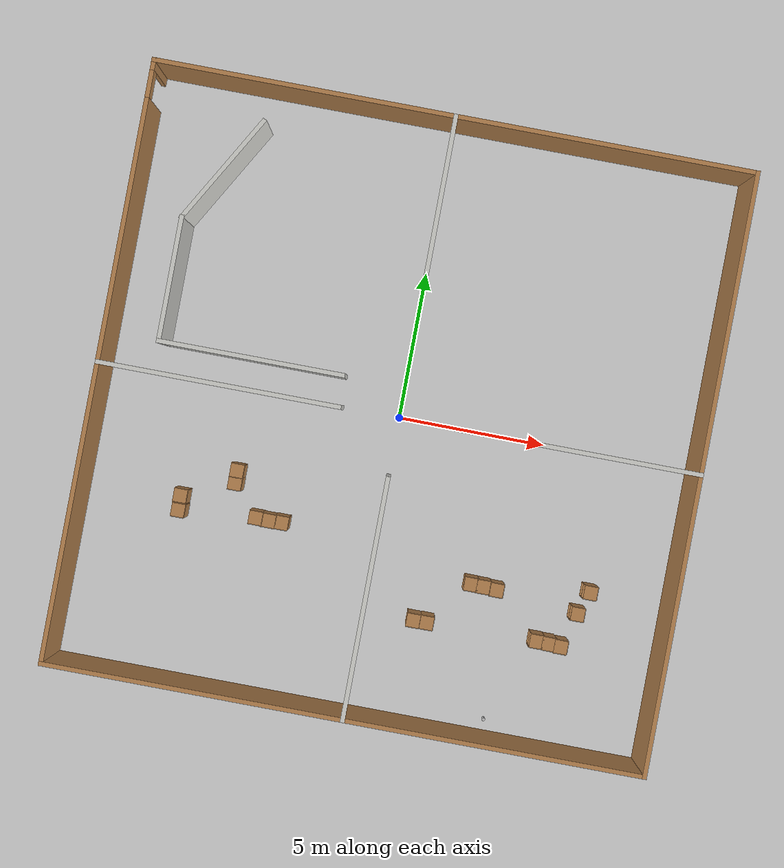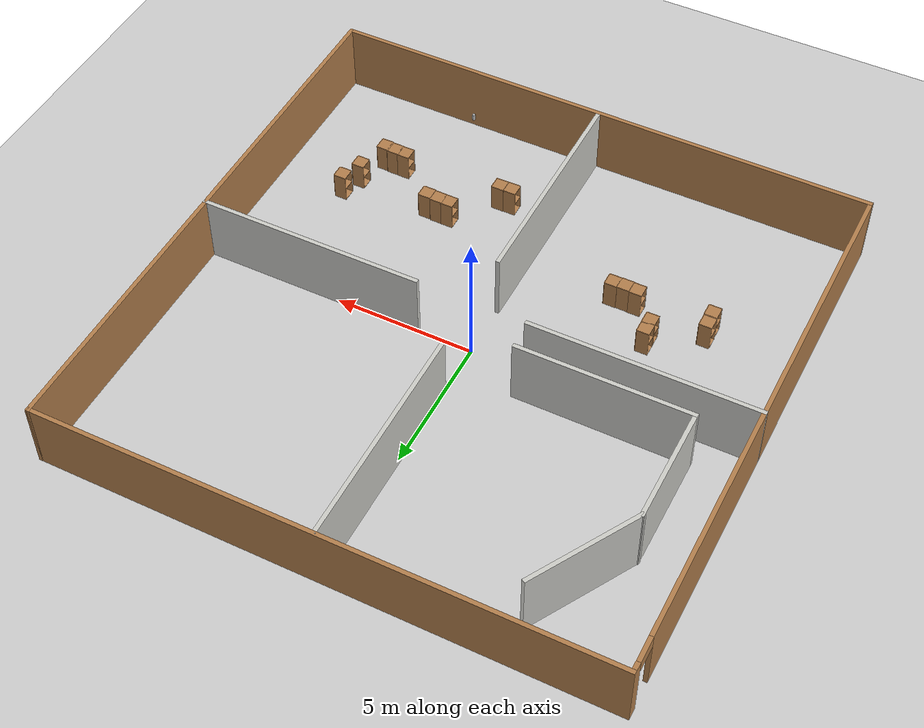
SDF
<sdf version="1.6">
 <world name="default">
  <light name="sun" type="directional">
   <pose>0 0 10 0 -0 0</pose>
   <diffuse>0.8 0.8 0.8 1</diffuse>
   <specular>0.2 0.2 0.2 1</specular>
   <attenuation>
    <range>1000</range>
    <constant>0.9</constant>
    <linear>0.01</linear>
    <quadratic>0.001</quadratic>
   </attenuation>
   <direction>-0.5 0.1 -0.9</direction>
  </light>
  <model name="ground_plane">
   <static>1</static>
   <link name="link">
    <collision name="collision">
     <geometry><plane><normal>0 0 1</normal><size>100 100</size></plane></geometry>
     <surface>
      <contact><collide_bitmask>65535</collide_bitmask></contact>
      <friction><ode><mu>100</mu><mu2>50</mu2></ode></friction>
     </surface>
    </collision>
    <visual name="visual">
     <cast_shadows>0</cast_shadows>
     <geometry><plane><normal>0 0 1</normal><size>100 100</size></plane></geometry>
     <material>
      <script><uri>file://media/materials/scripts/gazebo.material</uri><name>Gazebo/Grey</name></script>
     </material>
    </visual>
   </link>
  </model>
  <gravity>0 0 -9.8</gravity>
  <magnetic_field>6e-06 2.3e-05 -4.2e-05</magnetic_field>
  <atmosphere type="adiabatic"/>
  <physics name="default_physics" default="0" type="ode">
   <max_step_size>0.001</max_step_size>
   <real_time_factor>1</real_time_factor>
   <real_time_update_rate>1000</real_time_update_rate>
  </physics>
  <scene><ambient>0.4 0.4 0.4 1</ambient><background>0.7 0.7 0.7 1</background><shadows>1</shadows></scene>
  <audio><device>default</device></audio>
  <spherical_coordinates>
   <surface_model>EARTH_WGS84</surface_model>
   <latitude_deg>0</latitude_deg>
   <longitude_deg>0</longitude_deg>
   <elevation>0</elevation>
   <heading_deg>0</heading_deg>
  </spherical_coordinates>
  <model name="Sample_house">
   <link name="Wall_14">
    <collision name="Wall_14_Collision">
     <geometry><box><size>8.15 0.15 2.5</size></box></geometry>
     <pose>0 0 1.25 0 -0 0</pose>
    </collision>
    <visual name="Wall_14_Visual">
     <pose>0 0 1.25 0 -0 0</pose>
     <geometry><box><size>8.15 0.15 2.5</size></box></geometry>
     <material>
      <script><uri>file://media/materials/scripts/gazebo.material</uri><name>Gazebo/CeilingTiled</name></script>
      <ambient>0.435294 0.796078 0.67451 1</ambient>
     </material>
     <meta><layer>0</layer></meta>
    </visual>
    <pose>0 6 0 0 -0 -1.5708</pose>
   </link>
   <link name="Wall_16">
    <collision name="Wall_16_Collision">
     <geometry><box><size>8.15 0.15 2.5</size></box></geometry>
     <pose>0 0 1.25 0 -0 0</pose>
    </collision>
    <visual name="Wall_16_Visual">
     <pose>0 0 1.25 0 -0 0</pose>
     <geometry><box><size>8.15 0.15 2.5</size></box></geometry>
     <material>
      <script><uri>file://media/materials/scripts/gazebo.material</uri><name>Gazebo/CeilingTiled</name></script>
      <ambient>0.435294 0.796078 0.67451 1</ambient>
     </material>
     <meta><layer>0</layer></meta>
    </visual>
    <pose>-6 0 0 0 -0 0</pose>
   </link>
   <link name="Wall_18">
    <collision name="Wall_18_Collision">
     <geometry><box><size>8.15 0.15 2.5</size></box></geometry>
     <pose>0 0 1.25 0 -0 0</pose>
    </collision>
    <visual name="Wall_18_Visual">
     <pose>0 0 1.25 0 -0 0</pose>
     <geometry><box><size>8.15 0.15 2.5</size></box></geometry>
     <material>
      <script><uri>file://media/materials/scripts/gazebo.material</uri><name>Gazebo/CeilingTiled</name></script>
      <ambient>0.435294 0.796078 0.67451 1</ambient>
     </material>
     <meta><layer>0</layer></meta>
    </visual>
    <pose>0 -6 0 0 -0 1.5708</pose>
   </link>
   <link name="Wall_20">
    <collision name="Wall_20_Collision">
     <geometry><box><size>8.15 0.15 2.5</size></box></geometry>
     <pose>0 0 1.25 0 -0 0</pose>
    </collision>
    <visual name="Wall_20_Visual">
     <pose>0 0 1.25 0 -0 0</pose>
     <geometry><box><size>8.15 0.15 2.5</size></box></geometry>
     <material>
      <script><uri>file://media/materials/scripts/gazebo.material</uri><name>Gazebo/CeilingTiled</name></script>
      <ambient>0.435294 0.796078 0.67451 1</ambient>
     </material>
     <meta><layer>0</layer></meta>
    </visual>
    <pose>6 0 0 0 -0 3.14159</pose>
   </link>
   <link name="Wall_22">
    <collision name="Wall_22_Collision">
     <geometry><box><size>6.25 0.15 2.5</size></box></geometry>
     <pose>0 0 1.25 0 -0 0</pose>
    </collision>
    <visual name="Wall_22_Visual">
     <pose>0 0 1.25 0 -0 0</pose>
     <geometry><box><size>6.25 0.15 2.5</size></box></geometry>
     <material>
      <script><uri>file://media/materials/scripts/gazebo.material</uri><name>Gazebo/CeilingTiled</name></script>
      <ambient>0.435294 0.796078 0.67451 1</ambient>
     </material>
     <meta><layer>0</layer></meta>
    </visual>
    <pose>-5.12092 1.03734 0 0 -0 0</pose>
   </link>
   <link name="Wall_24">
    <collision name="Wall_24_Collision">
     <geometry><box><size>4.25 0.15 2.5</size></box></geometry>
     <pose>0 0 1.25 0 -0 0</pose>
    </collision>
    <visual name="Wall_24_Visual">
     <pose>0 0 1.25 0 -0 0</pose>
     <geometry><box><size>4.25 0.15 2.5</size></box></geometry>
     <material>
      <script><uri>file://media/materials/scripts/gazebo.material</uri><name>Gazebo/CeilingTiled</name></script>
      <ambient>0.435294 0.796078 0.67451 1</ambient>
     </material>
     <meta><layer>0</layer></meta>
    </visual>
    <pose>-8.17092 3.08734 0 0 -0 1.5708</pose>
   </link>
   <link name="Wall_25">
    <collision name="Wall_25_Collision">
     <geometry><box><size>4.25 0.15 2.5</size></box></geometry>
     <pose>0 0 1.25 0 -0 0</pose>
    </collision>
    <visual name="Wall_25_Visual">
     <pose>0 0 1.25 0 -0 0</pose>
     <geometry><box><size>4.25 0.15 2.5</size></box></geometry>
     <material>
      <script><uri>file://media/materials/scripts/gazebo.material</uri><name>Gazebo/CeilingTiled</name></script>
      <ambient>0.435294 0.796078 0.67451 1</ambient>
     </material>
     <meta><layer>0</layer></meta>
    </visual>
    <pose>-7.14592 6.91269 0 0 -0 1.0472</pose>
   </link>
   <link name="Wall_5">
    <collision name="Wall_5_Collision">
     <geometry><box><size>20.15 0.15 2.5</size></box></geometry>
     <pose>0 0 1.25 0 -0 0</pose>
    </collision>
    <visual name="Wall_5_Visual">
     <pose>0 0 1.25 0 -0 0</pose>
     <geometry><box><size>20.15 0.15 2.5</size></box></geometry>
     <material>
      <script><uri>file://media/materials/scripts/gazebo.material</uri><name>Gazebo/Wood</name></script>
      <ambient>0.996078 0.47451 0.0196078 1</ambient>
     </material>
     <meta><layer>0</layer></meta>
    </visual>
    <pose>10 0 0 0 -0 -1.5708</pose>
   </link>
   <link name="Wall_6">
    <collision name="Wall_6_Collision">
     <geometry><box><size>20.15 0.15 2.5</size></box></geometry>
     <pose>0 0 1.25 0 -0 0</pose>
    </collision>
    <visual name="Wall_6_Visual">
     <pose>0 0 1.25 0 -0 0</pose>
     <geometry><box><size>20.15 0.15 2.5</size></box></geometry>
     <material>
      <script><uri>file://media/materials/scripts/gazebo.material</uri><name>Gazebo/Wood</name></script>
      <ambient>0.996078 0.47451 0.0196078 1</ambient>
     </material>
     <meta><layer>0</layer></meta>
    </visual>
    <pose>0 -10 0 0 -0 3.14159</pose>
   </link>
   <link name="Wall_7">
    <pose>-10 0 0 0 -0 1.5708</pose>
    <visual name="Wall_7_Visual_0">
     <pose>-0.66033 0 1.25 0 -0 0</pose>
     <geometry><box><size>18.8293 0.15 2.5</size></box></geometry>
     <material>
      <script><uri>file://media/materials/scripts/gazebo.material</uri><name>Gazebo/Wood</name></script>
      <ambient>0.996078 0.47451 0.0196078 1</ambient>
     </material>
     <meta><layer>0</layer></meta>
    </visual>
    <collision name="Wall_7_Collision_0">
     <geometry><box><size>18.8293 0.15 2.5</size></box></geometry>
     <pose>-0.66033 0 1.25 0 -0 0</pose>
    </collision>
    <visual name="Wall_7_Visual_1">
     <pose>9.86467 0 1.25 0 -0 0</pose>
     <geometry><box><size>0.420661 0.15 2.5</size></box></geometry>
     <material>
      <script><uri>file://media/materials/scripts/gazebo.material</uri><name>Gazebo/Wood</name></script>
      <ambient>0.996078 0.47451 0.0196078 1</ambient>
     </material>
     <meta><layer>0</layer></meta>
    </visual>
    <collision name="Wall_7_Collision_1">
     <geometry><box><size>0.420661 0.15 2.5</size></box></geometry>
     <pose>9.86467 0 1.25 0 -0 0</pose>
    </collision>
    <visual name="Wall_7_Visual_2">
     <pose>9.20434 0 2.25 0 -0 0</pose>
     <geometry><box><size>0.9 0.15 0.5</size></box></geometry>
     <material>
      <script><uri>file://media/materials/scripts/gazebo.material</uri><name>Gazebo/Wood</name></script>
      <ambient>0.996078 0.47451 0.0196078 1</ambient>
     </material>
     <meta><layer>0</layer></meta>
    </visual>
    <collision name="Wall_7_Collision_2">
     <geometry><box><size>0.9 0.15 0.5</size></box></geometry>
     <pose>9.20434 0 2.25 0 -0 0</pose>
    </collision>
   </link>
   <link name="Wall_8">
    <collision name="Wall_8_Collision">
     <geometry><box><size>20.15 0.15 2.5</size></box></geometry>
     <pose>0 0 1.25 0 -0 0</pose>
    </collision>
    <visual name="Wall_8_Visual">
     <pose>0 0 1.25 0 -0 0</pose>
     <geometry><box><size>20.15 0.15 2.5</size></box></geometry>
     <material>
      <script><uri>file://media/materials/scripts/gazebo.material</uri><name>Gazebo/Wood</name></script>
      <ambient>0.996078 0.47451 0.0196078 1</ambient>
     </material>
     <meta><layer>0</layer></meta>
    </visual>
    <pose>0 10 0 0 -0 0</pose>
   </link>
   <static>1</static>
  </model>
  <model name="cabinet">
   <static>1</static>
   <link name="cabinet_bottom_plate">
    <inertial>
     <pose>0 0 -1 0 -0 0</pose>
     <inertia><ixx>2.05</ixx><ixy>0</ixy><ixz>0</ixz><iyy>2.05</iyy><iyz>0</iyz><izz>2.05</izz></inertia>
     <mass>25</mass>
    </inertial>
    <collision name="cabinet_bottom_plate_geom">
     <pose>0 0 0.01 0 -0 0</pose>
     <geometry><box><size>0.45 0.45 0.02</size></box></geometry>
    </collision>
    <visual name="cabinet_bottom_plate_geom_visual">
     <pose>0 0 0.01 0 -0 0</pose>
     <geometry><box><size>0.45 0.45 0.02</size></box></geometry>
     <material>
      <script><uri>file://media/materials/scripts/gazebo.material</uri><name>Gazebo/Wood</name></script>
     </material>
    </visual>
    <collision name="cabinet_bottom_plate_geom_cabinet_back_plate">
     <pose>0.235 0 0.51 0 -0 0</pose>
     <geometry><box><size>0.02 0.45 1.02</size></box></geometry>
    </collision>
    <visual name="cabinet_bottom_plate_geom_cabinet_back_plate_visual">
     <pose>0.235 0 0.51 0 -0 0</pose>
     <geometry><box><size>0.02 0.45 1.02</size></box></geometry>
     <material>
      <script><uri>file://media/materials/scripts/gazebo.material</uri><name>Gazebo/Wood</name></script>
     </material>
    </visual>
    <collision name="cabinet_bottom_plate_geom_cabinet_left_plate">
     <pose>0 0.235 0.51 0 -0 0</pose>
     <geometry><box><size>0.45 0.02 1.02</size></box></geometry>
    </collision>
    <visual name="cabinet_bottom_plate_geom_cabinet_left_plate_visual">
     <pose>0 0.235 0.51 0 -0 0</pose>
     <geometry><box><size>0.45 0.02 1.02</size></box></geometry>
     <material>
      <script><uri>file://media/materials/scripts/gazebo.material</uri><name>Gazebo/Wood</name></script>
     </material>
    </visual>
    <collision name="cabinet_bottom_plate_geom_cabinet_middle_plate">
     <pose>0 0 0.51 0 -0 0</pose>
     <geometry><box><size>0.45 0.45 0.02</size></box></geometry>
    </collision>
    <visual name="cabinet_bottom_plate_geom_cabinet_middle_plate_visual">
     <pose>0 0 0.51 0 -0 0</pose>
     <geometry><box><size>0.45 0.45 0.02</size></box></geometry>
     <material>
      <script><uri>file://media/materials/scripts/gazebo.material</uri><name>Gazebo/Wood</name></script>
     </material>
    </visual>
    <collision name="cabinet_bottom_plate_geom_cabinet_right_plate">
     <pose>0 -0.235 0.51 0 -0 0</pose>
     <geometry><box><size>0.45 0.02 1.02</size></box></geometry>
    </collision>
    <visual name="cabinet_bottom_plate_geom_cabinet_right_plate_visual">
     <pose>0 -0.235 0.51 0 -0 0</pose>
     <geometry><box><size>0.45 0.02 1.02</size></box></geometry>
     <material>
      <script><uri>file://media/materials/scripts/gazebo.material</uri><name>Gazebo/Wood</name></script>
     </material>
    </visual>
    <collision name="cabinet_bottom_plate_geom_cabinet_top_plate">
     <pose>0 0 1.01 0 -0 0</pose>
     <geometry><box><size>0.45 0.45 0.02</size></box></geometry>
    </collision>
    <visual name="cabinet_bottom_plate_geom_cabinet_top_plate_visual">
     <pose>0 0 1.01 0 -0 0</pose>
     <geometry><box><size>0.45 0.45 0.02</size></box></geometry>
     <material>
      <script><uri>file://media/materials/scripts/gazebo.material</uri><name>Gazebo/Wood</name></script>
     </material>
    </visual>
   </link>
   <pose>-4.12589 -4.16756 0 0 -0 0</pose>
  </model>
  <model name="cabinet_0">
   <static>1</static>
   <link name="cabinet_bottom_plate">
    <inertial>
     <pose>0 0 -1 0 -0 0</pose>
     <inertia><ixx>2.05</ixx><ixy>0</ixy><ixz>0</ixz><iyy>2.05</iyy><iyz>0</iyz><izz>2.05</izz></inertia>
     <mass>25</mass>
    </inertial>
    <collision name="cabinet_bottom_plate_geom">
     <pose>0 0 0.01 0 -0 0</pose>
     <geometry><box><size>0.45 0.45 0.02</size></box></geometry>
    </collision>
    <visual name="cabinet_bottom_plate_geom_visual">
     <pose>0 0 0.01 0 -0 0</pose>
     <geometry><box><size>0.45 0.45 0.02</size></box></geometry>
     <material>
      <script><uri>file://media/materials/scripts/gazebo.material</uri><name>Gazebo/Wood</name></script>
     </material>
    </visual>
    <collision name="cabinet_bottom_plate_geom_cabinet_back_plate">
     <pose>0.235 0 0.51 0 -0 0</pose>
     <geometry><box><size>0.02 0.45 1.02</size></box></geometry>
    </collision>
    <visual name="cabinet_bottom_plate_geom_cabinet_back_plate_visual">
     <pose>0.235 0 0.51 0 -0 0</pose>
     <geometry><box><size>0.02 0.45 1.02</size></box></geometry>
     <material>
      <script><uri>file://media/materials/scripts/gazebo.material</uri><name>Gazebo/Wood</name></script>
     </material>
    </visual>
    <collision name="cabinet_bottom_plate_geom_cabinet_left_plate">
     <pose>0 0.235 0.51 0 -0 0</pose>
     <geometry><box><size>0.45 0.02 1.02</size></box></geometry>
    </collision>
    <visual name="cabinet_bottom_plate_geom_cabinet_left_plate_visual">
     <pose>0 0.235 0.51 0 -0 0</pose>
     <geometry><box><size>0.45 0.02 1.02</size></box></geometry>
     <material>
      <script><uri>file://media/materials/scripts/gazebo.material</uri><name>Gazebo/Wood</name></script>
     </material>
    </visual>
    <collision name="cabinet_bottom_plate_geom_cabinet_middle_plate">
     <pose>0 0 0.51 0 -0 0</pose>
     <geometry><box><size>0.45 0.45 0.02</size></box></geometry>
    </collision>
    <visual name="cabinet_bottom_plate_geom_cabinet_middle_plate_visual">
     <pose>0 0 0.51 0 -0 0</pose>
     <geometry><box><size>0.45 0.45 0.02</size></box></geometry>
     <material>
      <script><uri>file://media/materials/scripts/gazebo.material</uri><name>Gazebo/Wood</name></script>
     </material>
    </visual>
    <collision name="cabinet_bottom_plate_geom_cabinet_right_plate">
     <pose>0 -0.235 0.51 0 -0 0</pose>
     <geometry><box><size>0.45 0.02 1.02</size></box></geometry>
    </collision>
    <visual name="cabinet_bottom_plate_geom_cabinet_right_plate_visual">
     <pose>0 -0.235 0.51 0 -0 0</pose>
     <geometry><box><size>0.45 0.02 1.02</size></box></geometry>
     <material>
      <script><uri>file://media/materials/scripts/gazebo.material</uri><name>Gazebo/Wood</name></script>
     </material>
    </visual>
    <collision name="cabinet_bottom_plate_geom_cabinet_top_plate">
     <pose>0 0 1.01 0 -0 0</pose>
     <geometry><box><size>0.45 0.45 0.02</size></box></geometry>
    </collision>
    <visual name="cabinet_bottom_plate_geom_cabinet_top_plate_visual">
     <pose>0 0 1.01 0 -0 0</pose>
     <geometry><box><size>0.45 0.45 0.02</size></box></geometry>
     <material>
      <script><uri>file://media/materials/scripts/gazebo.material</uri><name>Gazebo/Wood</name></script>
     </material>
    </visual>
   </link>
   <pose>-3.67632 -4.18228 0 0 -0 0</pose>
  </model>
  <model name="cabinet_1">
   <static>1</static>
   <link name="cabinet_bottom_plate">
    <inertial>
     <pose>0 0 -1 0 -0 0</pose>
     <inertia><ixx>2.05</ixx><ixy>0</ixy><ixz>0</ixz><iyy>2.05</iyy><iyz>0</iyz><izz>2.05</izz></inertia>
     <mass>25</mass>
    </inertial>
    <collision name="cabinet_bottom_plate_geom">
     <pose>0 0 0.01 0 -0 0</pose>
     <geometry><box><size>0.45 0.45 0.02</size></box></geometry>
    </collision>
    <visual name="cabinet_bottom_plate_geom_visual">
     <pose>0 0 0.01 0 -0 0</pose>
     <geometry><box><size>0.45 0.45 0.02</size></box></geometry>
     <material>
      <script><uri>file://media/materials/scripts/gazebo.material</uri><name>Gazebo/Wood</name></script>
     </material>
    </visual>
    <collision name="cabinet_bottom_plate_geom_cabinet_back_plate">
     <pose>0.235 0 0.51 0 -0 0</pose>
     <geometry><box><size>0.02 0.45 1.02</size></box></geometry>
    </collision>
    <visual name="cabinet_bottom_plate_geom_cabinet_back_plate_visual">
     <pose>0.235 0 0.51 0 -0 0</pose>
     <geometry><box><size>0.02 0.45 1.02</size></box></geometry>
     <material>
      <script><uri>file://media/materials/scripts/gazebo.material</uri><name>Gazebo/Wood</name></script>
     </material>
    </visual>
    <collision name="cabinet_bottom_plate_geom_cabinet_left_plate">
     <pose>0 0.235 0.51 0 -0 0</pose>
     <geometry><box><size>0.45 0.02 1.02</size></box></geometry>
    </collision>
    <visual name="cabinet_bottom_plate_geom_cabinet_left_plate_visual">
     <pose>0 0.235 0.51 0 -0 0</pose>
     <geometry><box><size>0.45 0.02 1.02</size></box></geometry>
     <material>
      <script><uri>file://media/materials/scripts/gazebo.material</uri><name>Gazebo/Wood</name></script>
     </material>
    </visual>
    <collision name="cabinet_bottom_plate_geom_cabinet_middle_plate">
     <pose>0 0 0.51 0 -0 0</pose>
     <geometry><box><size>0.45 0.45 0.02</size></box></geometry>
    </collision>
    <visual name="cabinet_bottom_plate_geom_cabinet_middle_plate_visual">
     <pose>0 0 0.51 0 -0 0</pose>
     <geometry><box><size>0.45 0.45 0.02</size></box></geometry>
     <material>
      <script><uri>file://media/materials/scripts/gazebo.material</uri><name>Gazebo/Wood</name></script>
     </material>
    </visual>
    <collision name="cabinet_bottom_plate_geom_cabinet_right_plate">
     <pose>0 -0.235 0.51 0 -0 0</pose>
     <geometry><box><size>0.45 0.02 1.02</size></box></geometry>
    </collision>
    <visual name="cabinet_bottom_plate_geom_cabinet_right_plate_visual">
     <pose>0 -0.235 0.51 0 -0 0</pose>
     <geometry><box><size>0.45 0.02 1.02</size></box></geometry>
     <material>
      <script><uri>file://media/materials/scripts/gazebo.material</uri><name>Gazebo/Wood</name></script>
     </material>
    </visual>
    <collision name="cabinet_bottom_plate_geom_cabinet_top_plate">
     <pose>0 0 1.01 0 -0 0</pose>
     <geometry><box><size>0.45 0.45 0.02</size></box></geometry>
    </collision>
    <visual name="cabinet_bottom_plate_geom_cabinet_top_plate_visual">
     <pose>0 0 1.01 0 -0 0</pose>
     <geometry><box><size>0.45 0.45 0.02</size></box></geometry>
     <material>
      <script><uri>file://media/materials/scripts/gazebo.material</uri><name>Gazebo/Wood</name></script>
     </material>
    </visual>
   </link>
   <pose>-3.23374 -4.17124 0 0 -0 0</pose>
  </model>
  <model name="beer">
   <link name="link">
    <pose>0 0 0.115 0 -0 0</pose>
    <inertial>
     <mass>0.39</mass>
     <inertia><ixx>0.00058</ixx><ixy>0</ixy><ixz>0</ixz><iyy>0.00058</iyy><iyz>0</iyz><izz>0.00019</izz></inertia>
    </inertial>
    <collision name="collision">
     <geometry><cylinder><radius>0.055</radius><length>0.23</length></cylinder></geometry>
    </collision>
    <visual name="visual">
     <geometry><cylinder><radius>0.055</radius><length>0.23</length></cylinder></geometry>
     <material>
      <script>
       <uri>model://beer/materials/scripts</uri>
       <uri>model://beer/materials/textures</uri>
       <name>Beer/Diffuse</name>
      </script>
     </material>
    </visual>
   </link>
   <pose>4.63252 -9.39475 0.774993 1.1e-05 5e-05 -0.000105</pose>
  </model>
  <model name="cabinet_2">
   <static>1</static>
   <link name="cabinet_bottom_plate">
    <inertial>
     <pose>0 0 -1 0 -0 0</pose>
     <inertia><ixx>2.05</ixx><ixy>0</ixy><ixz>0</ixz><iyy>2.05</iyy><iyz>0</iyz><izz>2.05</izz></inertia>
     <mass>25</mass>
    </inertial>
    <collision name="cabinet_bottom_plate_geom">
     <pose>0 0 0.01 0 -0 0</pose>
     <geometry><box><size>0.45 0.45 0.02</size></box></geometry>
    </collision>
    <visual name="cabinet_bottom_plate_geom_visual">
     <pose>0 0 0.01 0 -0 0</pose>
     <geometry><box><size>0.45 0.45 0.02</size></box></geometry>
     <material>
      <script><uri>file://media/materials/scripts/gazebo.material</uri><name>Gazebo/Wood</name></script>
     </material>
    </visual>
    <collision name="cabinet_bottom_plate_geom_cabinet_back_plate">
     <pose>0.235 0 0.51 0 -0 0</pose>
     <geometry><box><size>0.02 0.45 1.02</size></box></geometry>
    </collision>
    <visual name="cabinet_bottom_plate_geom_cabinet_back_plate_visual">
     <pose>0.235 0 0.51 0 -0 0</pose>
     <geometry><box><size>0.02 0.45 1.02</size></box></geometry>
     <material>
      <script><uri>file://media/materials/scripts/gazebo.material</uri><name>Gazebo/Wood</name></script>
     </material>
    </visual>
    <collision name="cabinet_bottom_plate_geom_cabinet_left_plate">
     <pose>0 0.235 0.51 0 -0 0</pose>
     <geometry><box><size>0.45 0.02 1.02</size></box></geometry>
    </collision>
    <visual name="cabinet_bottom_plate_geom_cabinet_left_plate_visual">
     <pose>0 0.235 0.51 0 -0 0</pose>
     <geometry><box><size>0.45 0.02 1.02</size></box></geometry>
     <material>
      <script><uri>file://media/materials/scripts/gazebo.material</uri><name>Gazebo/Wood</name></script>
     </material>
    </visual>
    <collision name="cabinet_bottom_plate_geom_cabinet_middle_plate">
     <pose>0 0 0.51 0 -0 0</pose>
     <geometry><box><size>0.45 0.45 0.02</size></box></geometry>
    </collision>
    <visual name="cabinet_bottom_plate_geom_cabinet_middle_plate_visual">
     <pose>0 0 0.51 0 -0 0</pose>
     <geometry><box><size>0.45 0.45 0.02</size></box></geometry>
     <material>
      <script><uri>file://media/materials/scripts/gazebo.material</uri><name>Gazebo/Wood</name></script>
     </material>
    </visual>
    <collision name="cabinet_bottom_plate_geom_cabinet_right_plate">
     <pose>0 -0.235 0.51 0 -0 0</pose>
     <geometry><box><size>0.45 0.02 1.02</size></box></geometry>
    </collision>
    <visual name="cabinet_bottom_plate_geom_cabinet_right_plate_visual">
     <pose>0 -0.235 0.51 0 -0 0</pose>
     <geometry><box><size>0.45 0.02 1.02</size></box></geometry>
     <material>
      <script><uri>file://media/materials/scripts/gazebo.material</uri><name>Gazebo/Wood</name></script>
     </material>
    </visual>
    <collision name="cabinet_bottom_plate_geom_cabinet_top_plate">
     <pose>0 0 1.01 0 -0 0</pose>
     <geometry><box><size>0.45 0.45 0.02</size></box></geometry>
    </collision>
    <visual name="cabinet_bottom_plate_geom_cabinet_top_plate_visual">
     <pose>0 0 1.01 0 -0 0</pose>
     <geometry><box><size>0.45 0.45 0.02</size></box></geometry>
     <material>
      <script><uri>file://media/materials/scripts/gazebo.material</uri><name>Gazebo/Wood</name></script>
     </material>
    </visual>
   </link>
   <pose>6.7359 -6.53452 0 0 -0 0</pose>
  </model>
  <model name="cabinet_3">
   <static>1</static>
   <link name="cabinet_bottom_plate">
    <inertial>
     <pose>0 0 -1 0 -0 0</pose>
     <inertia><ixx>2.05</ixx><ixy>0</ixy><ixz>0</ixz><iyy>2.05</iyy><iyz>0</iyz><izz>2.05</izz></inertia>
     <mass>25</mass>
    </inertial>
    <collision name="cabinet_bottom_plate_geom">
     <pose>0 0 0.01 0 -0 0</pose>
     <geometry><box><size>0.45 0.45 0.02</size></box></geometry>
    </collision>
    <visual name="cabinet_bottom_plate_geom_visual">
     <pose>0 0 0.01 0 -0 0</pose>
     <geometry><box><size>0.45 0.45 0.02</size></box></geometry>
     <material>
      <script><uri>file://media/materials/scripts/gazebo.material</uri><name>Gazebo/Wood</name></script>
     </material>
    </visual>
    <collision name="cabinet_bottom_plate_geom_cabinet_back_plate">
     <pose>0.235 0 0.51 0 -0 0</pose>
     <geometry><box><size>0.02 0.45 1.02</size></box></geometry>
    </collision>
    <visual name="cabinet_bottom_plate_geom_cabinet_back_plate_visual">
     <pose>0.235 0 0.51 0 -0 0</pose>
     <geometry><box><size>0.02 0.45 1.02</size></box></geometry>
     <material>
      <script><uri>file://media/materials/scripts/gazebo.material</uri><name>Gazebo/Wood</name></script>
     </material>
    </visual>
    <collision name="cabinet_bottom_plate_geom_cabinet_left_plate">
     <pose>0 0.235 0.51 0 -0 0</pose>
     <geometry><box><size>0.45 0.02 1.02</size></box></geometry>
    </collision>
    <visual name="cabinet_bottom_plate_geom_cabinet_left_plate_visual">
     <pose>0 0.235 0.51 0 -0 0</pose>
     <geometry><box><size>0.45 0.02 1.02</size></box></geometry>
     <material>
      <script><uri>file://media/materials/scripts/gazebo.material</uri><name>Gazebo/Wood</name></script>
     </material>
    </visual>
    <collision name="cabinet_bottom_plate_geom_cabinet_middle_plate">
     <pose>0 0 0.51 0 -0 0</pose>
     <geometry><box><size>0.45 0.45 0.02</size></box></geometry>
    </collision>
    <visual name="cabinet_bottom_plate_geom_cabinet_middle_plate_visual">
     <pose>0 0 0.51 0 -0 0</pose>
     <geometry><box><size>0.45 0.45 0.02</size></box></geometry>
     <material>
      <script><uri>file://media/materials/scripts/gazebo.material</uri><name>Gazebo/Wood</name></script>
     </material>
    </visual>
    <collision name="cabinet_bottom_plate_geom_cabinet_right_plate">
     <pose>0 -0.235 0.51 0 -0 0</pose>
     <geometry><box><size>0.45 0.02 1.02</size></box></geometry>
    </collision>
    <visual name="cabinet_bottom_plate_geom_cabinet_right_plate_visual">
     <pose>0 -0.235 0.51 0 -0 0</pose>
     <geometry><box><size>0.45 0.02 1.02</size></box></geometry>
     <material>
      <script><uri>file://media/materials/scripts/gazebo.material</uri><name>Gazebo/Wood</name></script>
     </material>
    </visual>
    <collision name="cabinet_bottom_plate_geom_cabinet_top_plate">
     <pose>0 0 1.01 0 -0 0</pose>
     <geometry><box><size>0.45 0.45 0.02</size></box></geometry>
    </collision>
    <visual name="cabinet_bottom_plate_geom_cabinet_top_plate_visual">
     <pose>0 0 1.01 0 -0 0</pose>
     <geometry><box><size>0.45 0.45 0.02</size></box></geometry>
     <material>
      <script><uri>file://media/materials/scripts/gazebo.material</uri><name>Gazebo/Wood</name></script>
     </material>
    </visual>
   </link>
   <pose>6.31648 -6.511 0 0 -0 0</pose>
  </model>
  <model name="cabinet_4">
   <static>1</static>
   <link name="cabinet_bottom_plate">
    <inertial>
     <pose>0 0 -1 0 -0 0</pose>
     <inertia><ixx>2.05</ixx><ixy>0</ixy><ixz>0</ixz><iyy>2.05</iyy><iyz>0</iyz><izz>2.05</izz></inertia>
     <mass>25</mass>
    </inertial>
    <collision name="cabinet_bottom_plate_geom">
     <pose>0 0 0.01 0 -0 0</pose>
     <geometry><box><size>0.45 0.45 0.02</size></box></geometry>
    </collision>
    <visual name="cabinet_bottom_plate_geom_visual">
     <pose>0 0 0.01 0 -0 0</pose>
     <geometry><box><size>0.45 0.45 0.02</size></box></geometry>
     <material>
      <script><uri>file://media/materials/scripts/gazebo.material</uri><name>Gazebo/Wood</name></script>
     </material>
    </visual>
    <collision name="cabinet_bottom_plate_geom_cabinet_back_plate">
     <pose>0.235 0 0.51 0 -0 0</pose>
     <geometry><box><size>0.02 0.45 1.02</size></box></geometry>
    </collision>
    <visual name="cabinet_bottom_plate_geom_cabinet_back_plate_visual">
     <pose>0.235 0 0.51 0 -0 0</pose>
     <geometry><box><size>0.02 0.45 1.02</size></box></geometry>
     <material>
      <script><uri>file://media/materials/scripts/gazebo.material</uri><name>Gazebo/Wood</name></script>
     </material>
    </visual>
    <collision name="cabinet_bottom_plate_geom_cabinet_left_plate">
     <pose>0 0.235 0.51 0 -0 0</pose>
     <geometry><box><size>0.45 0.02 1.02</size></box></geometry>
    </collision>
    <visual name="cabinet_bottom_plate_geom_cabinet_left_plate_visual">
     <pose>0 0.235 0.51 0 -0 0</pose>
     <geometry><box><size>0.45 0.02 1.02</size></box></geometry>
     <material>
      <script><uri>file://media/materials/scripts/gazebo.material</uri><name>Gazebo/Wood</name></script>
     </material>
    </visual>
    <collision name="cabinet_bottom_plate_geom_cabinet_middle_plate">
     <pose>0 0 0.51 0 -0 0</pose>
     <geometry><box><size>0.45 0.45 0.02</size></box></geometry>
    </collision>
    <visual name="cabinet_bottom_plate_geom_cabinet_middle_plate_visual">
     <pose>0 0 0.51 0 -0 0</pose>
     <geometry><box><size>0.45 0.45 0.02</size></box></geometry>
     <material>
      <script><uri>file://media/materials/scripts/gazebo.material</uri><name>Gazebo/Wood</name></script>
     </material>
    </visual>
    <collision name="cabinet_bottom_plate_geom_cabinet_right_plate">
     <pose>0 -0.235 0.51 0 -0 0</pose>
     <geometry><box><size>0.45 0.02 1.02</size></box></geometry>
    </collision>
    <visual name="cabinet_bottom_plate_geom_cabinet_right_plate_visual">
     <pose>0 -0.235 0.51 0 -0 0</pose>
     <geometry><box><size>0.45 0.02 1.02</size></box></geometry>
     <material>
      <script><uri>file://media/materials/scripts/gazebo.material</uri><name>Gazebo/Wood</name></script>
     </material>
    </visual>
    <collision name="cabinet_bottom_plate_geom_cabinet_top_plate">
     <pose>0 0 1.01 0 -0 0</pose>
     <geometry><box><size>0.45 0.45 0.02</size></box></geometry>
    </collision>
    <visual name="cabinet_bottom_plate_geom_cabinet_top_plate_visual">
     <pose>0 0 1.01 0 -0 0</pose>
     <geometry><box><size>0.45 0.45 0.02</size></box></geometry>
     <material>
      <script><uri>file://media/materials/scripts/gazebo.material</uri><name>Gazebo/Wood</name></script>
     </material>
    </visual>
   </link>
   <pose>5.8994 -6.50101 0 0 -0 0</pose>
  </model>
  <model name="cabinet_5">
   <static>1</static>
   <link name="cabinet_bottom_plate">
    <inertial>
     <pose>0 0 -1 0 -0 0</pose>
     <inertia><ixx>2.05</ixx><ixy>0</ixy><ixz>0</ixz><iyy>2.05</iyy><iyz>0</iyz><izz>2.05</izz></inertia>
     <mass>25</mass>
    </inertial>
    <collision name="cabinet_bottom_plate_geom">
     <pose>0 0 0.01 0 -0 0</pose>
     <geometry><box><size>0.45 0.45 0.02</size></box></geometry>
    </collision>
    <visual name="cabinet_bottom_plate_geom_visual">
     <pose>0 0 0.01 0 -0 0</pose>
     <geometry><box><size>0.45 0.45 0.02</size></box></geometry>
     <material>
      <script><uri>file://media/materials/scripts/gazebo.material</uri><name>Gazebo/Wood</name></script>
     </material>
    </visual>
    <collision name="cabinet_bottom_plate_geom_cabinet_back_plate">
     <pose>0.235 0 0.51 0 -0 0</pose>
     <geometry><box><size>0.02 0.45 1.02</size></box></geometry>
    </collision>
    <visual name="cabinet_bottom_plate_geom_cabinet_back_plate_visual">
     <pose>0.235 0 0.51 0 -0 0</pose>
     <geometry><box><size>0.02 0.45 1.02</size></box></geometry>
     <material>
      <script><uri>file://media/materials/scripts/gazebo.material</uri><name>Gazebo/Wood</name></script>
     </material>
    </visual>
    <collision name="cabinet_bottom_plate_geom_cabinet_left_plate">
     <pose>0 0.235 0.51 0 -0 0</pose>
     <geometry><box><size>0.45 0.02 1.02</size></box></geometry>
    </collision>
    <visual name="cabinet_bottom_plate_geom_cabinet_left_plate_visual">
     <pose>0 0.235 0.51 0 -0 0</pose>
     <geometry><box><size>0.45 0.02 1.02</size></box></geometry>
     <material>
      <script><uri>file://media/materials/scripts/gazebo.material</uri><name>Gazebo/Wood</name></script>
     </material>
    </visual>
    <collision name="cabinet_bottom_plate_geom_cabinet_middle_plate">
     <pose>0 0 0.51 0 -0 0</pose>
     <geometry><box><size>0.45 0.45 0.02</size></box></geometry>
    </collision>
    <visual name="cabinet_bottom_plate_geom_cabinet_middle_plate_visual">
     <pose>0 0 0.51 0 -0 0</pose>
     <geometry><box><size>0.45 0.45 0.02</size></box></geometry>
     <material>
      <script><uri>file://media/materials/scripts/gazebo.material</uri><name>Gazebo/Wood</name></script>
     </material>
    </visual>
    <collision name="cabinet_bottom_plate_geom_cabinet_right_plate">
     <pose>0 -0.235 0.51 0 -0 0</pose>
     <geometry><box><size>0.45 0.02 1.02</size></box></geometry>
    </collision>
    <visual name="cabinet_bottom_plate_geom_cabinet_right_plate_visual">
     <pose>0 -0.235 0.51 0 -0 0</pose>
     <geometry><box><size>0.45 0.02 1.02</size></box></geometry>
     <material>
      <script><uri>file://media/materials/scripts/gazebo.material</uri><name>Gazebo/Wood</name></script>
     </material>
    </visual>
    <collision name="cabinet_bottom_plate_geom_cabinet_top_plate">
     <pose>0 0 1.01 0 -0 0</pose>
     <geometry><box><size>0.45 0.45 0.02</size></box></geometry>
    </collision>
    <visual name="cabinet_bottom_plate_geom_cabinet_top_plate_visual">
     <pose>0 0 1.01 0 -0 0</pose>
     <geometry><box><size>0.45 0.45 0.02</size></box></geometry>
     <material>
      <script><uri>file://media/materials/scripts/gazebo.material</uri><name>Gazebo/Wood</name></script>
     </material>
    </visual>
   </link>
   <pose>7.38638 -4.57138 0 0 -0 0</pose>
  </model>
  <model name="cabinet_6">
   <static>1</static>
   <link name="cabinet_bottom_plate">
    <inertial>
     <pose>0 0 -1 0 -0 0</pose>
     <inertia><ixx>2.05</ixx><ixy>0</ixy><ixz>0</ixz><iyy>2.05</iyy><iyz>0</iyz><izz>2.05</izz></inertia>
     <mass>25</mass>
    </inertial>
    <collision name="cabinet_bottom_plate_geom">
     <pose>0 0 0.01 0 -0 0</pose>
     <geometry><box><size>0.45 0.45 0.02</size></box></geometry>
    </collision>
    <visual name="cabinet_bottom_plate_geom_visual">
     <pose>0 0 0.01 0 -0 0</pose>
     <geometry><box><size>0.45 0.45 0.02</size></box></geometry>
     <material>
      <script><uri>file://media/materials/scripts/gazebo.material</uri><name>Gazebo/Wood</name></script>
     </material>
    </visual>
    <collision name="cabinet_bottom_plate_geom_cabinet_back_plate">
     <pose>0.235 0 0.51 0 -0 0</pose>
     <geometry><box><size>0.02 0.45 1.02</size></box></geometry>
    </collision>
    <visual name="cabinet_bottom_plate_geom_cabinet_back_plate_visual">
     <pose>0.235 0 0.51 0 -0 0</pose>
     <geometry><box><size>0.02 0.45 1.02</size></box></geometry>
     <material>
      <script><uri>file://media/materials/scripts/gazebo.material</uri><name>Gazebo/Wood</name></script>
     </material>
    </visual>
    <collision name="cabinet_bottom_plate_geom_cabinet_left_plate">
     <pose>0 0.235 0.51 0 -0 0</pose>
     <geometry><box><size>0.45 0.02 1.02</size></box></geometry>
    </collision>
    <visual name="cabinet_bottom_plate_geom_cabinet_left_plate_visual">
     <pose>0 0.235 0.51 0 -0 0</pose>
     <geometry><box><size>0.45 0.02 1.02</size></box></geometry>
     <material>
      <script><uri>file://media/materials/scripts/gazebo.material</uri><name>Gazebo/Wood</name></script>
     </material>
    </visual>
    <collision name="cabinet_bottom_plate_geom_cabinet_middle_plate">
     <pose>0 0 0.51 0 -0 0</pose>
     <geometry><box><size>0.45 0.45 0.02</size></box></geometry>
    </collision>
    <visual name="cabinet_bottom_plate_geom_cabinet_middle_plate_visual">
     <pose>0 0 0.51 0 -0 0</pose>
     <geometry><box><size>0.45 0.45 0.02</size></box></geometry>
     <material>
      <script><uri>file://media/materials/scripts/gazebo.material</uri><name>Gazebo/Wood</name></script>
     </material>
    </visual>
    <collision name="cabinet_bottom_plate_geom_cabinet_right_plate">
     <pose>0 -0.235 0.51 0 -0 0</pose>
     <geometry><box><size>0.45 0.02 1.02</size></box></geometry>
    </collision>
    <visual name="cabinet_bottom_plate_geom_cabinet_right_plate_visual">
     <pose>0 -0.235 0.51 0 -0 0</pose>
     <geometry><box><size>0.45 0.02 1.02</size></box></geometry>
     <material>
      <script><uri>file://media/materials/scripts/gazebo.material</uri><name>Gazebo/Wood</name></script>
     </material>
    </visual>
    <collision name="cabinet_bottom_plate_geom_cabinet_top_plate">
     <pose>0 0 1.01 0 -0 0</pose>
     <geometry><box><size>0.45 0.45 0.02</size></box></geometry>
    </collision>
    <visual name="cabinet_bottom_plate_geom_cabinet_top_plate_visual">
     <pose>0 0 1.01 0 -0 0</pose>
     <geometry><box><size>0.45 0.45 0.02</size></box></geometry>
     <material>
      <script><uri>file://media/materials/scripts/gazebo.material</uri><name>Gazebo/Wood</name></script>
     </material>
    </visual>
   </link>
   <pose>7.09521 -5.35379 0 0 -0 0</pose>
  </model>
  <model name="cabinet_7">
   <static>1</static>
   <link name="cabinet_bottom_plate">
    <inertial>
     <pose>0 0 -1 0 -0 0</pose>
     <inertia><ixx>2.05</ixx><ixy>0</ixy><ixz>0</ixz><iyy>2.05</iyy><iyz>0</iyz><izz>2.05</izz></inertia>
     <mass>25</mass>
    </inertial>
    <collision name="cabinet_bottom_plate_geom">
     <pose>0 0 0.01 0 -0 0</pose>
     <geometry><box><size>0.45 0.45 0.02</size></box></geometry>
    </collision>
    <visual name="cabinet_bottom_plate_geom_visual">
     <pose>0 0 0.01 0 -0 0</pose>
     <geometry><box><size>0.45 0.45 0.02</size></box></geometry>
     <material>
      <script><uri>file://media/materials/scripts/gazebo.material</uri><name>Gazebo/Wood</name></script>
     </material>
    </visual>
    <collision name="cabinet_bottom_plate_geom_cabinet_back_plate">
     <pose>0.235 0 0.51 0 -0 0</pose>
     <geometry><box><size>0.02 0.45 1.02</size></box></geometry>
    </collision>
    <visual name="cabinet_bottom_plate_geom_cabinet_back_plate_visual">
     <pose>0.235 0 0.51 0 -0 0</pose>
     <geometry><box><size>0.02 0.45 1.02</size></box></geometry>
     <material>
      <script><uri>file://media/materials/scripts/gazebo.material</uri><name>Gazebo/Wood</name></script>
     </material>
    </visual>
    <collision name="cabinet_bottom_plate_geom_cabinet_left_plate">
     <pose>0 0.235 0.51 0 -0 0</pose>
     <geometry><box><size>0.45 0.02 1.02</size></box></geometry>
    </collision>
    <visual name="cabinet_bottom_plate_geom_cabinet_left_plate_visual">
     <pose>0 0.235 0.51 0 -0 0</pose>
     <geometry><box><size>0.45 0.02 1.02</size></box></geometry>
     <material>
      <script><uri>file://media/materials/scripts/gazebo.material</uri><name>Gazebo/Wood</name></script>
     </material>
    </visual>
    <collision name="cabinet_bottom_plate_geom_cabinet_middle_plate">
     <pose>0 0 0.51 0 -0 0</pose>
     <geometry><box><size>0.45 0.45 0.02</size></box></geometry>
    </collision>
    <visual name="cabinet_bottom_plate_geom_cabinet_middle_plate_visual">
     <pose>0 0 0.51 0 -0 0</pose>
     <geometry><box><size>0.45 0.45 0.02</size></box></geometry>
     <material>
      <script><uri>file://media/materials/scripts/gazebo.material</uri><name>Gazebo/Wood</name></script>
     </material>
    </visual>
    <collision name="cabinet_bottom_plate_geom_cabinet_right_plate">
     <pose>0 -0.235 0.51 0 -0 0</pose>
     <geometry><box><size>0.45 0.02 1.02</size></box></geometry>
    </collision>
    <visual name="cabinet_bottom_plate_geom_cabinet_right_plate_visual">
     <pose>0 -0.235 0.51 0 -0 0</pose>
     <geometry><box><size>0.45 0.02 1.02</size></box></geometry>
     <material>
      <script><uri>file://media/materials/scripts/gazebo.material</uri><name>Gazebo/Wood</name></script>
     </material>
    </visual>
    <collision name="cabinet_bottom_plate_geom_cabinet_top_plate">
     <pose>0 0 1.01 0 -0 0</pose>
     <geometry><box><size>0.45 0.45 0.02</size></box></geometry>
    </collision>
    <visual name="cabinet_bottom_plate_geom_cabinet_top_plate_visual">
     <pose>0 0 1.01 0 -0 0</pose>
     <geometry><box><size>0.45 0.45 0.02</size></box></geometry>
     <material>
      <script><uri>file://media/materials/scripts/gazebo.material</uri><name>Gazebo/Wood</name></script>
     </material>
    </visual>
   </link>
   <pose>-5.02692 -2.72778 0 0 -0 0</pose>
  </model>
  <model name="cabinet_8">
   <static>1</static>
   <link name="cabinet_bottom_plate">
    <inertial>
     <pose>0 0 -1 0 -0 0</pose>
     <inertia><ixx>2.05</ixx><ixy>0</ixy><ixz>0</ixz><iyy>2.05</iyy><iyz>0</iyz><izz>2.05</izz></inertia>
     <mass>25</mass>
    </inertial>
    <collision name="cabinet_bottom_plate_geom">
     <pose>0 0 0.01 0 -0 0</pose>
     <geometry><box><size>0.45 0.45 0.02</size></box></geometry>
    </collision>
    <visual name="cabinet_bottom_plate_geom_visual">
     <pose>0 0 0.01 0 -0 0</pose>
     <geometry><box><size>0.45 0.45 0.02</size></box></geometry>
     <material>
      <script><uri>file://media/materials/scripts/gazebo.material</uri><name>Gazebo/Wood</name></script>
     </material>
    </visual>
    <collision name="cabinet_bottom_plate_geom_cabinet_back_plate">
     <pose>0.235 0 0.51 0 -0 0</pose>
     <geometry><box><size>0.02 0.45 1.02</size></box></geometry>
    </collision>
    <visual name="cabinet_bottom_plate_geom_cabinet_back_plate_visual">
     <pose>0.235 0 0.51 0 -0 0</pose>
     <geometry><box><size>0.02 0.45 1.02</size></box></geometry>
     <material>
      <script><uri>file://media/materials/scripts/gazebo.material</uri><name>Gazebo/Wood</name></script>
     </material>
    </visual>
    <collision name="cabinet_bottom_plate_geom_cabinet_left_plate">
     <pose>0 0.235 0.51 0 -0 0</pose>
     <geometry><box><size>0.45 0.02 1.02</size></box></geometry>
    </collision>
    <visual name="cabinet_bottom_plate_geom_cabinet_left_plate_visual">
     <pose>0 0.235 0.51 0 -0 0</pose>
     <geometry><box><size>0.45 0.02 1.02</size></box></geometry>
     <material>
      <script><uri>file://media/materials/scripts/gazebo.material</uri><name>Gazebo/Wood</name></script>
     </material>
    </visual>
    <collision name="cabinet_bottom_plate_geom_cabinet_middle_plate">
     <pose>0 0 0.51 0 -0 0</pose>
     <geometry><box><size>0.45 0.45 0.02</size></box></geometry>
    </collision>
    <visual name="cabinet_bottom_plate_geom_cabinet_middle_plate_visual">
     <pose>0 0 0.51 0 -0 0</pose>
     <geometry><box><size>0.45 0.45 0.02</size></box></geometry>
     <material>
      <script><uri>file://media/materials/scripts/gazebo.material</uri><name>Gazebo/Wood</name></script>
     </material>
    </visual>
    <collision name="cabinet_bottom_plate_geom_cabinet_right_plate">
     <pose>0 -0.235 0.51 0 -0 0</pose>
     <geometry><box><size>0.45 0.02 1.02</size></box></geometry>
    </collision>
    <visual name="cabinet_bottom_plate_geom_cabinet_right_plate_visual">
     <pose>0 -0.235 0.51 0 -0 0</pose>
     <geometry><box><size>0.45 0.02 1.02</size></box></geometry>
     <material>
      <script><uri>file://media/materials/scripts/gazebo.material</uri><name>Gazebo/Wood</name></script>
     </material>
    </visual>
    <collision name="cabinet_bottom_plate_geom_cabinet_top_plate">
     <pose>0 0 1.01 0 -0 0</pose>
     <geometry><box><size>0.45 0.45 0.02</size></box></geometry>
    </collision>
    <visual name="cabinet_bottom_plate_geom_cabinet_top_plate_visual">
     <pose>0 0 1.01 0 -0 0</pose>
     <geometry><box><size>0.45 0.45 0.02</size></box></geometry>
     <material>
      <script><uri>file://media/materials/scripts/gazebo.material</uri><name>Gazebo/Wood</name></script>
     </material>
    </visual>
   </link>
   <pose>-6.72622 -4.3907 0 0 -0 0</pose>
  </model>
  <model name="cabinet_9">
   <static>1</static>
   <link name="cabinet_bottom_plate">
    <inertial>
     <pose>0 0 -1 0 -0 0</pose>
     <inertia><ixx>2.05</ixx><ixy>0</ixy><ixz>0</ixz><iyy>2.05</iyy><iyz>0</iyz><izz>2.05</izz></inertia>
     <mass>25</mass>
    </inertial>
    <collision name="cabinet_bottom_plate_geom">
     <pose>0 0 0.01 0 -0 0</pose>
     <geometry><box><size>0.45 0.45 0.02</size></box></geometry>
    </collision>
    <visual name="cabinet_bottom_plate_geom_visual">
     <pose>0 0 0.01 0 -0 0</pose>
     <geometry><box><size>0.45 0.45 0.02</size></box></geometry>
     <material>
      <script><uri>file://media/materials/scripts/gazebo.material</uri><name>Gazebo/Wood</name></script>
     </material>
    </visual>
    <collision name="cabinet_bottom_plate_geom_cabinet_back_plate">
     <pose>0.235 0 0.51 0 -0 0</pose>
     <geometry><box><size>0.02 0.45 1.02</size></box></geometry>
    </collision>
    <visual name="cabinet_bottom_plate_geom_cabinet_back_plate_visual">
     <pose>0.235 0 0.51 0 -0 0</pose>
     <geometry><box><size>0.02 0.45 1.02</size></box></geometry>
     <material>
      <script><uri>file://media/materials/scripts/gazebo.material</uri><name>Gazebo/Wood</name></script>
     </material>
    </visual>
    <collision name="cabinet_bottom_plate_geom_cabinet_left_plate">
     <pose>0 0.235 0.51 0 -0 0</pose>
     <geometry><box><size>0.45 0.02 1.02</size></box></geometry>
    </collision>
    <visual name="cabinet_bottom_plate_geom_cabinet_left_plate_visual">
     <pose>0 0.235 0.51 0 -0 0</pose>
     <geometry><box><size>0.45 0.02 1.02</size></box></geometry>
     <material>
      <script><uri>file://media/materials/scripts/gazebo.material</uri><name>Gazebo/Wood</name></script>
     </material>
    </visual>
    <collision name="cabinet_bottom_plate_geom_cabinet_middle_plate">
     <pose>0 0 0.51 0 -0 0</pose>
     <geometry><box><size>0.45 0.45 0.02</size></box></geometry>
    </collision>
    <visual name="cabinet_bottom_plate_geom_cabinet_middle_plate_visual">
     <pose>0 0 0.51 0 -0 0</pose>
     <geometry><box><size>0.45 0.45 0.02</size></box></geometry>
     <material>
      <script><uri>file://media/materials/scripts/gazebo.material</uri><name>Gazebo/Wood</name></script>
     </material>
    </visual>
    <collision name="cabinet_bottom_plate_geom_cabinet_right_plate">
     <pose>0 -0.235 0.51 0 -0 0</pose>
     <geometry><box><size>0.45 0.02 1.02</size></box></geometry>
    </collision>
    <visual name="cabinet_bottom_plate_geom_cabinet_right_plate_visual">
     <pose>0 -0.235 0.51 0 -0 0</pose>
     <geometry><box><size>0.45 0.02 1.02</size></box></geometry>
     <material>
      <script><uri>file://media/materials/scripts/gazebo.material</uri><name>Gazebo/Wood</name></script>
     </material>
    </visual>
    <collision name="cabinet_bottom_plate_geom_cabinet_top_plate">
     <pose>0 0 1.01 0 -0 0</pose>
     <geometry><box><size>0.45 0.45 0.02</size></box></geometry>
    </collision>
    <visual name="cabinet_bottom_plate_geom_cabinet_top_plate_visual">
     <pose>0 0 1.01 0 -0 0</pose>
     <geometry><box><size>0.45 0.45 0.02</size></box></geometry>
     <material>
      <script><uri>file://media/materials/scripts/gazebo.material</uri><name>Gazebo/Wood</name></script>
     </material>
    </visual>
   </link>
   <pose>-5.01974 -3.15442 0 0 -0 0</pose>
  </model>
  <model name="cabinet_10">
   <static>1</static>
   <link name="cabinet_bottom_plate">
    <inertial>
     <pose>0 0 -1 0 -0 0</pose>
     <inertia><ixx>2.05</ixx><ixy>0</ixy><ixz>0</ixz><iyy>2.05</iyy><iyz>0</iyz><izz>2.05</izz></inertia>
     <mass>25</mass>
    </inertial>
    <collision name="cabinet_bottom_plate_geom">
     <pose>0 0 0.01 0 -0 0</pose>
     <geometry><box><size>0.45 0.45 0.02</size></box></geometry>
    </collision>
    <visual name="cabinet_bottom_plate_geom_visual">
     <pose>0 0 0.01 0 -0 0</pose>
     <geometry><box><size>0.45 0.45 0.02</size></box></geometry>
     <material>
      <script><uri>file://media/materials/scripts/gazebo.material</uri><name>Gazebo/Wood</name></script>
     </material>
    </visual>
    <collision name="cabinet_bottom_plate_geom_cabinet_back_plate">
     <pose>0.235 0 0.51 0 -0 0</pose>
     <geometry><box><size>0.02 0.45 1.02</size></box></geometry>
    </collision>
    <visual name="cabinet_bottom_plate_geom_cabinet_back_plate_visual">
     <pose>0.235 0 0.51 0 -0 0</pose>
     <geometry><box><size>0.02 0.45 1.02</size></box></geometry>
     <material>
      <script><uri>file://media/materials/scripts/gazebo.material</uri><name>Gazebo/Wood</name></script>
     </material>
    </visual>
    <collision name="cabinet_bottom_plate_geom_cabinet_left_plate">
     <pose>0 0.235 0.51 0 -0 0</pose>
     <geometry><box><size>0.45 0.02 1.02</size></box></geometry>
    </collision>
    <visual name="cabinet_bottom_plate_geom_cabinet_left_plate_visual">
     <pose>0 0.235 0.51 0 -0 0</pose>
     <geometry><box><size>0.45 0.02 1.02</size></box></geometry>
     <material>
      <script><uri>file://media/materials/scripts/gazebo.material</uri><name>Gazebo/Wood</name></script>
     </material>
    </visual>
    <collision name="cabinet_bottom_plate_geom_cabinet_middle_plate">
     <pose>0 0 0.51 0 -0 0</pose>
     <geometry><box><size>0.45 0.45 0.02</size></box></geometry>
    </collision>
    <visual name="cabinet_bottom_plate_geom_cabinet_middle_plate_visual">
     <pose>0 0 0.51 0 -0 0</pose>
     <geometry><box><size>0.45 0.45 0.02</size></box></geometry>
     <material>
      <script><uri>file://media/materials/scripts/gazebo.material</uri><name>Gazebo/Wood</name></script>
     </material>
    </visual>
    <collision name="cabinet_bottom_plate_geom_cabinet_right_plate">
     <pose>0 -0.235 0.51 0 -0 0</pose>
     <geometry><box><size>0.45 0.02 1.02</size></box></geometry>
    </collision>
    <visual name="cabinet_bottom_plate_geom_cabinet_right_plate_visual">
     <pose>0 -0.235 0.51 0 -0 0</pose>
     <geometry><box><size>0.45 0.02 1.02</size></box></geometry>
     <material>
      <script><uri>file://media/materials/scripts/gazebo.material</uri><name>Gazebo/Wood</name></script>
     </material>
    </visual>
    <collision name="cabinet_bottom_plate_geom_cabinet_top_plate">
     <pose>0 0 1.01 0 -0 0</pose>
     <geometry><box><size>0.45 0.45 0.02</size></box></geometry>
    </collision>
    <visual name="cabinet_bottom_plate_geom_cabinet_top_plate_visual">
     <pose>0 0 1.01 0 -0 0</pose>
     <geometry><box><size>0.45 0.45 0.02</size></box></geometry>
     <material>
      <script><uri>file://media/materials/scripts/gazebo.material</uri><name>Gazebo/Wood</name></script>
     </material>
    </visual>
   </link>
   <pose>-6.74271 -3.89788 0 0 -0 0</pose>
  </model>
  <model name="cabinet_11">
   <static>1</static>
   <link name="cabinet_bottom_plate">
    <inertial>
     <pose>0 0 -1 0 -0 0</pose>
     <inertia><ixx>2.05</ixx><ixy>0</ixy><ixz>0</ixz><iyy>2.05</iyy><iyz>0</iyz><izz>2.05</izz></inertia>
     <mass>25</mass>
    </inertial>
    <collision name="cabinet_bottom_plate_geom">
     <pose>0 0 0.01 0 -0 0</pose>
     <geometry><box><size>0.45 0.45 0.02</size></box></geometry>
    </collision>
    <visual name="cabinet_bottom_plate_geom_visual">
     <pose>0 0 0.01 0 -0 0</pose>
     <geometry><box><size>0.45 0.45 0.02</size></box></geometry>
     <material>
      <script><uri>file://media/materials/scripts/gazebo.material</uri><name>Gazebo/Wood</name></script>
     </material>
    </visual>
    <collision name="cabinet_bottom_plate_geom_cabinet_back_plate">
     <pose>0.235 0 0.51 0 -0 0</pose>
     <geometry><box><size>0.02 0.45 1.02</size></box></geometry>
    </collision>
    <visual name="cabinet_bottom_plate_geom_cabinet_back_plate_visual">
     <pose>0.235 0 0.51 0 -0 0</pose>
     <geometry><box><size>0.02 0.45 1.02</size></box></geometry>
     <material>
      <script><uri>file://media/materials/scripts/gazebo.material</uri><name>Gazebo/Wood</name></script>
     </material>
    </visual>
    <collision name="cabinet_bottom_plate_geom_cabinet_left_plate">
     <pose>0 0.235 0.51 0 -0 0</pose>
     <geometry><box><size>0.45 0.02 1.02</size></box></geometry>
    </collision>
    <visual name="cabinet_bottom_plate_geom_cabinet_left_plate_visual">
     <pose>0 0.235 0.51 0 -0 0</pose>
     <geometry><box><size>0.45 0.02 1.02</size></box></geometry>
     <material>
      <script><uri>file://media/materials/scripts/gazebo.material</uri><name>Gazebo/Wood</name></script>
     </material>
    </visual>
    <collision name="cabinet_bottom_plate_geom_cabinet_middle_plate">
     <pose>0 0 0.51 0 -0 0</pose>
     <geometry><box><size>0.45 0.45 0.02</size></box></geometry>
    </collision>
    <visual name="cabinet_bottom_plate_geom_cabinet_middle_plate_visual">
     <pose>0 0 0.51 0 -0 0</pose>
     <geometry><box><size>0.45 0.45 0.02</size></box></geometry>
     <material>
      <script><uri>file://media/materials/scripts/gazebo.material</uri><name>Gazebo/Wood</name></script>
     </material>
    </visual>
    <collision name="cabinet_bottom_plate_geom_cabinet_right_plate">
     <pose>0 -0.235 0.51 0 -0 0</pose>
     <geometry><box><size>0.45 0.02 1.02</size></box></geometry>
    </collision>
    <visual name="cabinet_bottom_plate_geom_cabinet_right_plate_visual">
     <pose>0 -0.235 0.51 0 -0 0</pose>
     <geometry><box><size>0.45 0.02 1.02</size></box></geometry>
     <material>
      <script><uri>file://media/materials/scripts/gazebo.material</uri><name>Gazebo/Wood</name></script>
     </material>
    </visual>
    <collision name="cabinet_bottom_plate_geom_cabinet_top_plate">
     <pose>0 0 1.01 0 -0 0</pose>
     <geometry><box><size>0.45 0.45 0.02</size></box></geometry>
    </collision>
    <visual name="cabinet_bottom_plate_geom_cabinet_top_plate_visual">
     <pose>0 0 1.01 0 -0 0</pose>
     <geometry><box><size>0.45 0.45 0.02</size></box></geometry>
     <material>
      <script><uri>file://media/materials/scripts/gazebo.material</uri><name>Gazebo/Wood</name></script>
     </material>
    </visual>
   </link>
   <pose>4.27721 -5.05984 0 0 -0 0</pose>
  </model>
  <model name="cabinet_12">
   <static>1</static>
   <link name="cabinet_bottom_plate">
    <inertial>
     <pose>0 0 -1 0 -0 0</pose>
     <inertia><ixx>2.05</ixx><ixy>0</ixy><ixz>0</ixz><iyy>2.05</iyy><iyz>0</iyz><izz>2.05</izz></inertia>
     <mass>25</mass>
    </inertial>
    <collision name="cabinet_bottom_plate_geom">
     <pose>0 0 0.01 0 -0 0</pose>
     <geometry><box><size>0.45 0.45 0.02</size></box></geometry>
    </collision>
    <visual name="cabinet_bottom_plate_geom_visual">
     <pose>0 0 0.01 0 -0 0</pose>
     <geometry><box><size>0.45 0.45 0.02</size></box></geometry>
     <material>
      <script><uri>file://media/materials/scripts/gazebo.material</uri><name>Gazebo/Wood</name></script>
     </material>
    </visual>
    <collision name="cabinet_bottom_plate_geom_cabinet_back_plate">
     <pose>0.235 0 0.51 0 -0 0</pose>
     <geometry><box><size>0.02 0.45 1.02</size></box></geometry>
    </collision>
    <visual name="cabinet_bottom_plate_geom_cabinet_back_plate_visual">
     <pose>0.235 0 0.51 0 -0 0</pose>
     <geometry><box><size>0.02 0.45 1.02</size></box></geometry>
     <material>
      <script><uri>file://media/materials/scripts/gazebo.material</uri><name>Gazebo/Wood</name></script>
     </material>
    </visual>
    <collision name="cabinet_bottom_plate_geom_cabinet_left_plate">
     <pose>0 0.235 0.51 0 -0 0</pose>
     <geometry><box><size>0.45 0.02 1.02</size></box></geometry>
    </collision>
    <visual name="cabinet_bottom_plate_geom_cabinet_left_plate_visual">
     <pose>0 0.235 0.51 0 -0 0</pose>
     <geometry><box><size>0.45 0.02 1.02</size></box></geometry>
     <material>
      <script><uri>file://media/materials/scripts/gazebo.material</uri><name>Gazebo/Wood</name></script>
     </material>
    </visual>
    <collision name="cabinet_bottom_plate_geom_cabinet_middle_plate">
     <pose>0 0 0.51 0 -0 0</pose>
     <geometry><box><size>0.45 0.45 0.02</size></box></geometry>
    </collision>
    <visual name="cabinet_bottom_plate_geom_cabinet_middle_plate_visual">
     <pose>0 0 0.51 0 -0 0</pose>
     <geometry><box><size>0.45 0.45 0.02</size></box></geometry>
     <material>
      <script><uri>file://media/materials/scripts/gazebo.material</uri><name>Gazebo/Wood</name></script>
     </material>
    </visual>
    <collision name="cabinet_bottom_plate_geom_cabinet_right_plate">
     <pose>0 -0.235 0.51 0 -0 0</pose>
     <geometry><box><size>0.45 0.02 1.02</size></box></geometry>
    </collision>
    <visual name="cabinet_bottom_plate_geom_cabinet_right_plate_visual">
     <pose>0 -0.235 0.51 0 -0 0</pose>
     <geometry><box><size>0.45 0.02 1.02</size></box></geometry>
     <material>
      <script><uri>file://media/materials/scripts/gazebo.material</uri><name>Gazebo/Wood</name></script>
     </material>
    </visual>
    <collision name="cabinet_bottom_plate_geom_cabinet_top_plate">
     <pose>0 0 1.01 0 -0 0</pose>
     <geometry><box><size>0.45 0.45 0.02</size></box></geometry>
    </collision>
    <visual name="cabinet_bottom_plate_geom_cabinet_top_plate_visual">
     <pose>0 0 1.01 0 -0 0</pose>
     <geometry><box><size>0.45 0.45 0.02</size></box></geometry>
     <material>
      <script><uri>file://media/materials/scripts/gazebo.material</uri><name>Gazebo/Wood</name></script>
     </material>
    </visual>
   </link>
   <pose>3.80947 -5.03505 0 0 -0 0</pose>
  </model>
  <model name="cabinet_13">
   <static>1</static>
   <link name="cabinet_bottom_plate">
    <inertial>
     <pose>0 0 -1 0 -0 0</pose>
     <inertia><ixx>2.05</ixx><ixy>0</ixy><ixz>0</ixz><iyy>2.05</iyy><iyz>0</iyz><izz>2.05</izz></inertia>
     <mass>25</mass>
    </inertial>
    <collision name="cabinet_bottom_plate_geom">
     <pose>0 0 0.01 0 -0 0</pose>
     <geometry><box><size>0.45 0.45 0.02</size></box></geometry>
    </collision>
    <visual name="cabinet_bottom_plate_geom_visual">
     <pose>0 0 0.01 0 -0 0</pose>
     <geometry><box><size>0.45 0.45 0.02</size></box></geometry>
     <material>
      <script><uri>file://media/materials/scripts/gazebo.material</uri><name>Gazebo/Wood</name></script>
     </material>
    </visual>
    <collision name="cabinet_bottom_plate_geom_cabinet_back_plate">
     <pose>0.235 0 0.51 0 -0 0</pose>
     <geometry><box><size>0.02 0.45 1.02</size></box></geometry>
    </collision>
    <visual name="cabinet_bottom_plate_geom_cabinet_back_plate_visual">
     <pose>0.235 0 0.51 0 -0 0</pose>
     <geometry><box><size>0.02 0.45 1.02</size></box></geometry>
     <material>
      <script><uri>file://media/materials/scripts/gazebo.material</uri><name>Gazebo/Wood</name></script>
     </material>
    </visual>
    <collision name="cabinet_bottom_plate_geom_cabinet_left_plate">
     <pose>0 0.235 0.51 0 -0 0</pose>
     <geometry><box><size>0.45 0.02 1.02</size></box></geometry>
    </collision>
    <visual name="cabinet_bottom_plate_geom_cabinet_left_plate_visual">
     <pose>0 0.235 0.51 0 -0 0</pose>
     <geometry><box><size>0.45 0.02 1.02</size></box></geometry>
     <material>
      <script><uri>file://media/materials/scripts/gazebo.material</uri><name>Gazebo/Wood</name></script>
     </material>
    </visual>
    <collision name="cabinet_bottom_plate_geom_cabinet_middle_plate">
     <pose>0 0 0.51 0 -0 0</pose>
     <geometry><box><size>0.45 0.45 0.02</size></box></geometry>
    </collision>
    <visual name="cabinet_bottom_plate_geom_cabinet_middle_plate_visual">
     <pose>0 0 0.51 0 -0 0</pose>
     <geometry><box><size>0.45 0.45 0.02</size></box></geometry>
     <material>
      <script><uri>file://media/materials/scripts/gazebo.material</uri><name>Gazebo/Wood</name></script>
     </material>
    </visual>
    <collision name="cabinet_bottom_plate_geom_cabinet_right_plate">
     <pose>0 -0.235 0.51 0 -0 0</pose>
     <geometry><box><size>0.45 0.02 1.02</size></box></geometry>
    </collision>
    <visual name="cabinet_bottom_plate_geom_cabinet_right_plate_visual">
     <pose>0 -0.235 0.51 0 -0 0</pose>
     <geometry><box><size>0.45 0.02 1.02</size></box></geometry>
     <material>
      <script><uri>file://media/materials/scripts/gazebo.material</uri><name>Gazebo/Wood</name></script>
     </material>
    </visual>
    <collision name="cabinet_bottom_plate_geom_cabinet_top_plate">
     <pose>0 0 1.01 0 -0 0</pose>
     <geometry><box><size>0.45 0.45 0.02</size></box></geometry>
    </collision>
    <visual name="cabinet_bottom_plate_geom_cabinet_top_plate_visual">
     <pose>0 0 1.01 0 -0 0</pose>
     <geometry><box><size>0.45 0.45 0.02</size></box></geometry>
     <material>
      <script><uri>file://media/materials/scripts/gazebo.material</uri><name>Gazebo/Wood</name></script>
     </material>
    </visual>
   </link>
   <pose>3.38855 -5.02721 0 0 -0 0</pose>
  </model>
  <model name="cabinet_14">
   <static>1</static>
   <link name="cabinet_bottom_plate">
    <inertial>
     <pose>0 0 -1 0 -0 0</pose>
     <inertia><ixx>2.05</ixx><ixy>0</ixy><ixz>0</ixz><iyy>2.05</iyy><iyz>0</iyz><izz>2.05</izz></inertia>
     <mass>25</mass>
    </inertial>
    <collision name="cabinet_bottom_plate_geom">
     <pose>0 0 0.01 0 -0 0</pose>
     <geometry><box><size>0.45 0.45 0.02</size></box></geometry>
    </collision>
    <visual name="cabinet_bottom_plate_geom_visual">
     <pose>0 0 0.01 0 -0 0</pose>
     <geometry><box><size>0.45 0.45 0.02</size></box></geometry>
     <material>
      <script><uri>file://media/materials/scripts/gazebo.material</uri><name>Gazebo/Wood</name></script>
     </material>
    </visual>
    <collision name="cabinet_bottom_plate_geom_cabinet_back_plate">
     <pose>0.235 0 0.51 0 -0 0</pose>
     <geometry><box><size>0.02 0.45 1.02</size></box></geometry>
    </collision>
    <visual name="cabinet_bottom_plate_geom_cabinet_back_plate_visual">
     <pose>0.235 0 0.51 0 -0 0</pose>
     <geometry><box><size>0.02 0.45 1.02</size></box></geometry>
     <material>
      <script><uri>file://media/materials/scripts/gazebo.material</uri><name>Gazebo/Wood</name></script>
     </material>
    </visual>
    <collision name="cabinet_bottom_plate_geom_cabinet_left_plate">
     <pose>0 0.235 0.51 0 -0 0</pose>
     <geometry><box><size>0.45 0.02 1.02</size></box></geometry>
    </collision>
    <visual name="cabinet_bottom_plate_geom_cabinet_left_plate_visual">
     <pose>0 0.235 0.51 0 -0 0</pose>
     <geometry><box><size>0.45 0.02 1.02</size></box></geometry>
     <material>
      <script><uri>file://media/materials/scripts/gazebo.material</uri><name>Gazebo/Wood</name></script>
     </material>
    </visual>
    <collision name="cabinet_bottom_plate_geom_cabinet_middle_plate">
     <pose>0 0 0.51 0 -0 0</pose>
     <geometry><box><size>0.45 0.45 0.02</size></box></geometry>
    </collision>
    <visual name="cabinet_bottom_plate_geom_cabinet_middle_plate_visual">
     <pose>0 0 0.51 0 -0 0</pose>
     <geometry><box><size>0.45 0.45 0.02</size></box></geometry>
     <material>
      <script><uri>file://media/materials/scripts/gazebo.material</uri><name>Gazebo/Wood</name></script>
     </material>
    </visual>
    <collision name="cabinet_bottom_plate_geom_cabinet_right_plate">
     <pose>0 -0.235 0.51 0 -0 0</pose>
     <geometry><box><size>0.45 0.02 1.02</size></box></geometry>
    </collision>
    <visual name="cabinet_bottom_plate_geom_cabinet_right_plate_visual">
     <pose>0 -0.235 0.51 0 -0 0</pose>
     <geometry><box><size>0.45 0.02 1.02</size></box></geometry>
     <material>
      <script><uri>file://media/materials/scripts/gazebo.material</uri><name>Gazebo/Wood</name></script>
     </material>
    </visual>
    <collision name="cabinet_bottom_plate_geom_cabinet_top_plate">
     <pose>0 0 1.01 0 -0 0</pose>
     <geometry><box><size>0.45 0.45 0.02</size></box></geometry>
    </collision>
    <visual name="cabinet_bottom_plate_geom_cabinet_top_plate_visual">
     <pose>0 0 1.01 0 -0 0</pose>
     <geometry><box><size>0.45 0.45 0.02</size></box></geometry>
     <material>
      <script><uri>file://media/materials/scripts/gazebo.material</uri><name>Gazebo/Wood</name></script>
     </material>
    </visual>
   </link>
   <pose>2.1661 -6.56555 0 0 -0 0</pose>
  </model>
  <model name="cabinet_15">
   <static>1</static>
   <link name="cabinet_bottom_plate">
    <inertial>
     <pose>0 0 -1 0 -0 0</pose>
     <inertia><ixx>2.05</ixx><ixy>0</ixy><ixz>0</ixz><iyy>2.05</iyy><iyz>0</iyz><izz>2.05</izz></inertia>
     <mass>25</mass>
    </inertial>
    <collision name="cabinet_bottom_plate_geom">
     <pose>0 0 0.01 0 -0 0</pose>
     <geometry><box><size>0.45 0.45 0.02</size></box></geometry>
    </collision>
    <visual name="cabinet_bottom_plate_geom_visual">
     <pose>0 0 0.01 0 -0 0</pose>
     <geometry><box><size>0.45 0.45 0.02</size></box></geometry>
     <material>
      <script><uri>file://media/materials/scripts/gazebo.material</uri><name>Gazebo/Wood</name></script>
     </material>
    </visual>
    <collision name="cabinet_bottom_plate_geom_cabinet_back_plate">
     <pose>0.235 0 0.51 0 -0 0</pose>
     <geometry><box><size>0.02 0.45 1.02</size></box></geometry>
    </collision>
    <visual name="cabinet_bottom_plate_geom_cabinet_back_plate_visual">
     <pose>0.235 0 0.51 0 -0 0</pose>
     <geometry><box><size>0.02 0.45 1.02</size></box></geometry>
     <material>
      <script><uri>file://media/materials/scripts/gazebo.material</uri><name>Gazebo/Wood</name></script>
     </material>
    </visual>
    <collision name="cabinet_bottom_plate_geom_cabinet_left_plate">
     <pose>0 0.235 0.51 0 -0 0</pose>
     <geometry><box><size>0.45 0.02 1.02</size></box></geometry>
    </collision>
    <visual name="cabinet_bottom_plate_geom_cabinet_left_plate_visual">
     <pose>0 0.235 0.51 0 -0 0</pose>
     <geometry><box><size>0.45 0.02 1.02</size></box></geometry>
     <material>
      <script><uri>file://media/materials/scripts/gazebo.material</uri><name>Gazebo/Wood</name></script>
     </material>
    </visual>
    <collision name="cabinet_bottom_plate_geom_cabinet_middle_plate">
     <pose>0 0 0.51 0 -0 0</pose>
     <geometry><box><size>0.45 0.45 0.02</size></box></geometry>
    </collision>
    <visual name="cabinet_bottom_plate_geom_cabinet_middle_plate_visual">
     <pose>0 0 0.51 0 -0 0</pose>
     <geometry><box><size>0.45 0.45 0.02</size></box></geometry>
     <material>
      <script><uri>file://media/materials/scripts/gazebo.material</uri><name>Gazebo/Wood</name></script>
     </material>
    </visual>
    <collision name="cabinet_bottom_plate_geom_cabinet_right_plate">
     <pose>0 -0.235 0.51 0 -0 0</pose>
     <geometry><box><size>0.45 0.02 1.02</size></box></geometry>
    </collision>
    <visual name="cabinet_bottom_plate_geom_cabinet_right_plate_visual">
     <pose>0 -0.235 0.51 0 -0 0</pose>
     <geometry><box><size>0.45 0.02 1.02</size></box></geometry>
     <material>
      <script><uri>file://media/materials/scripts/gazebo.material</uri><name>Gazebo/Wood</name></script>
     </material>
    </visual>
    <collision name="cabinet_bottom_plate_geom_cabinet_top_plate">
     <pose>0 0 1.01 0 -0 0</pose>
     <geometry><box><size>0.45 0.45 0.02</size></box></geometry>
    </collision>
    <visual name="cabinet_bottom_plate_geom_cabinet_top_plate_visual">
     <pose>0 0 1.01 0 -0 0</pose>
     <geometry><box><size>0.45 0.45 0.02</size></box></geometry>
     <material>
      <script><uri>file://media/materials/scripts/gazebo.material</uri><name>Gazebo/Wood</name></script>
     </material>
    </visual>
   </link>
   <pose>1.7079 -6.57352 0 0 -0 0</pose>
  </model>
 </world>
</sdf>
